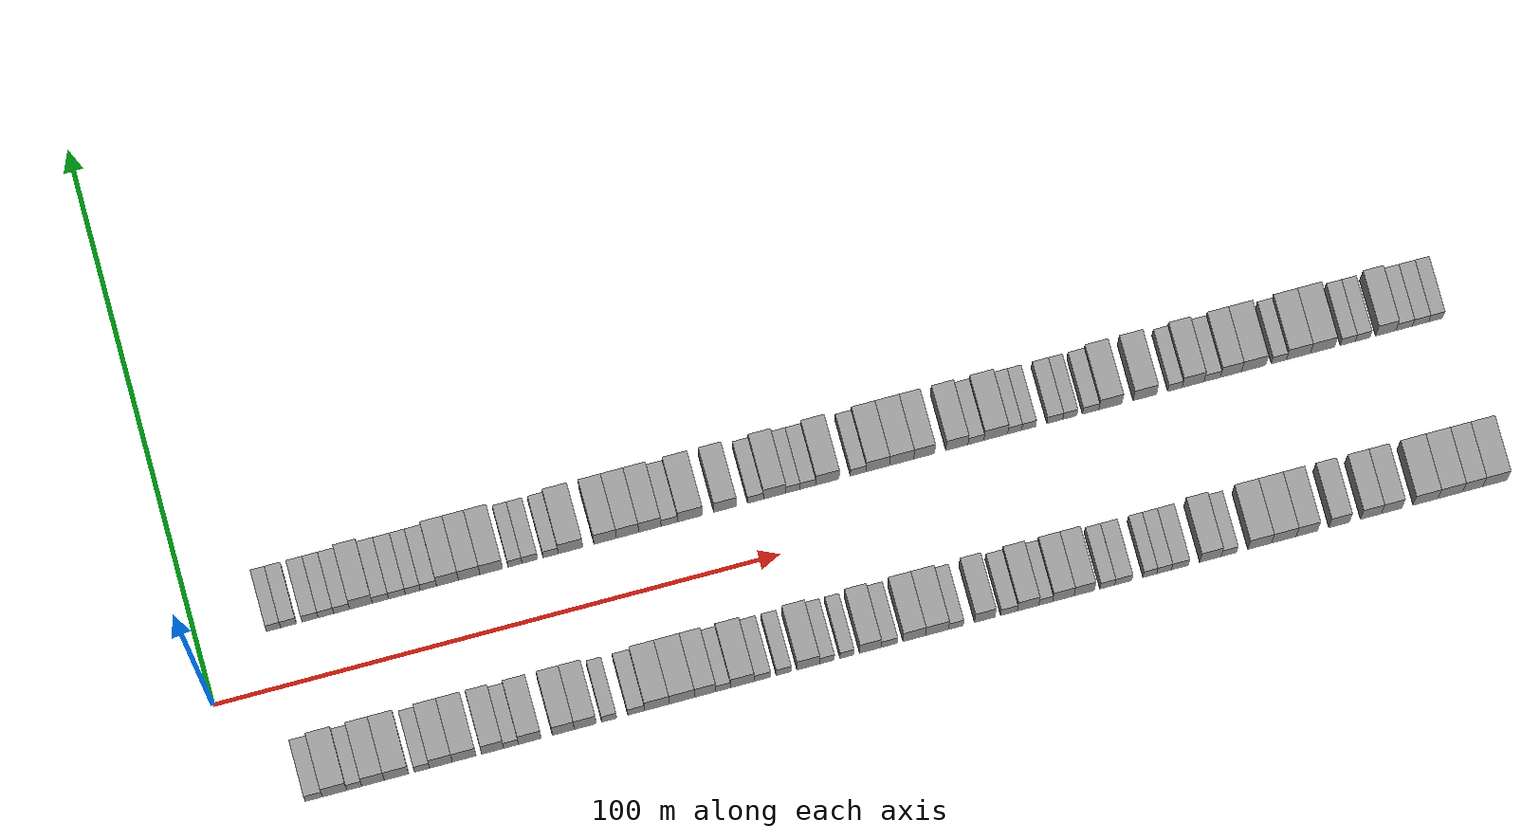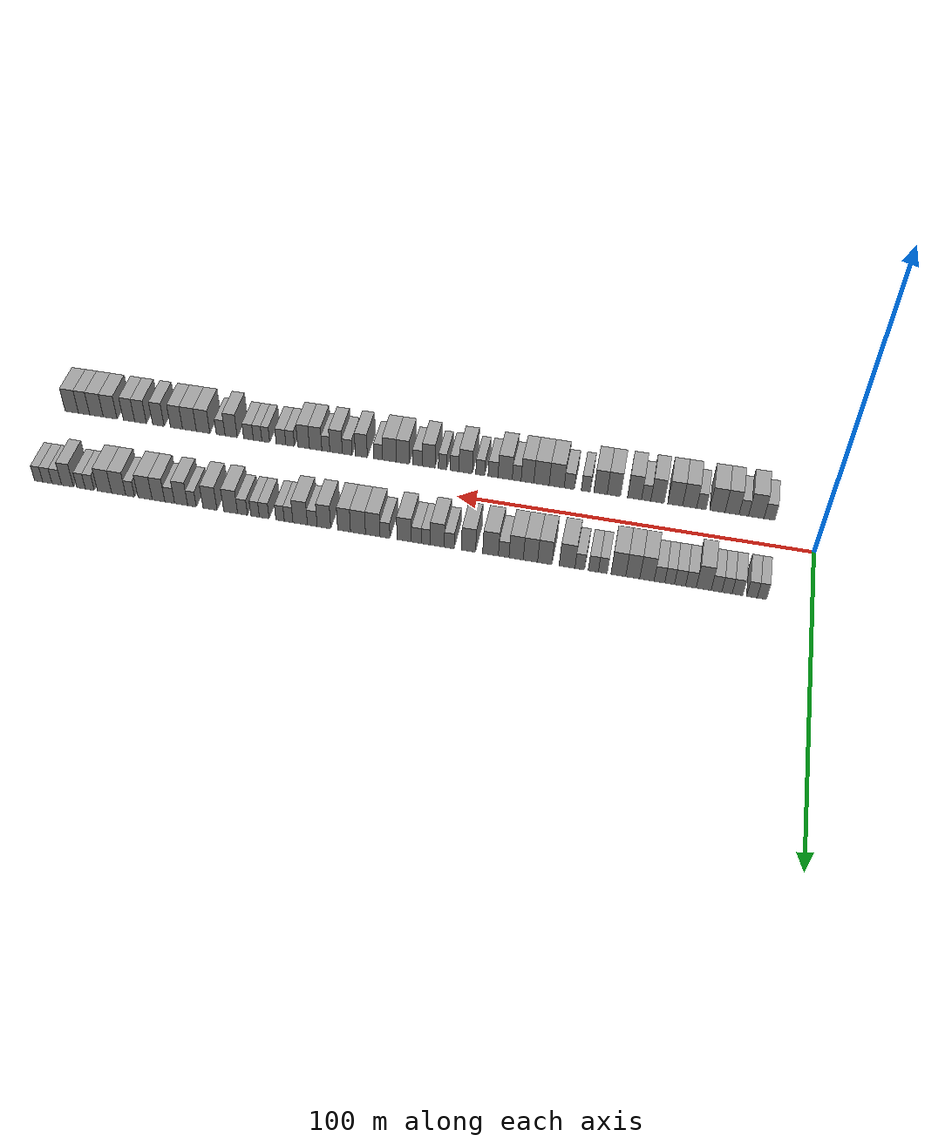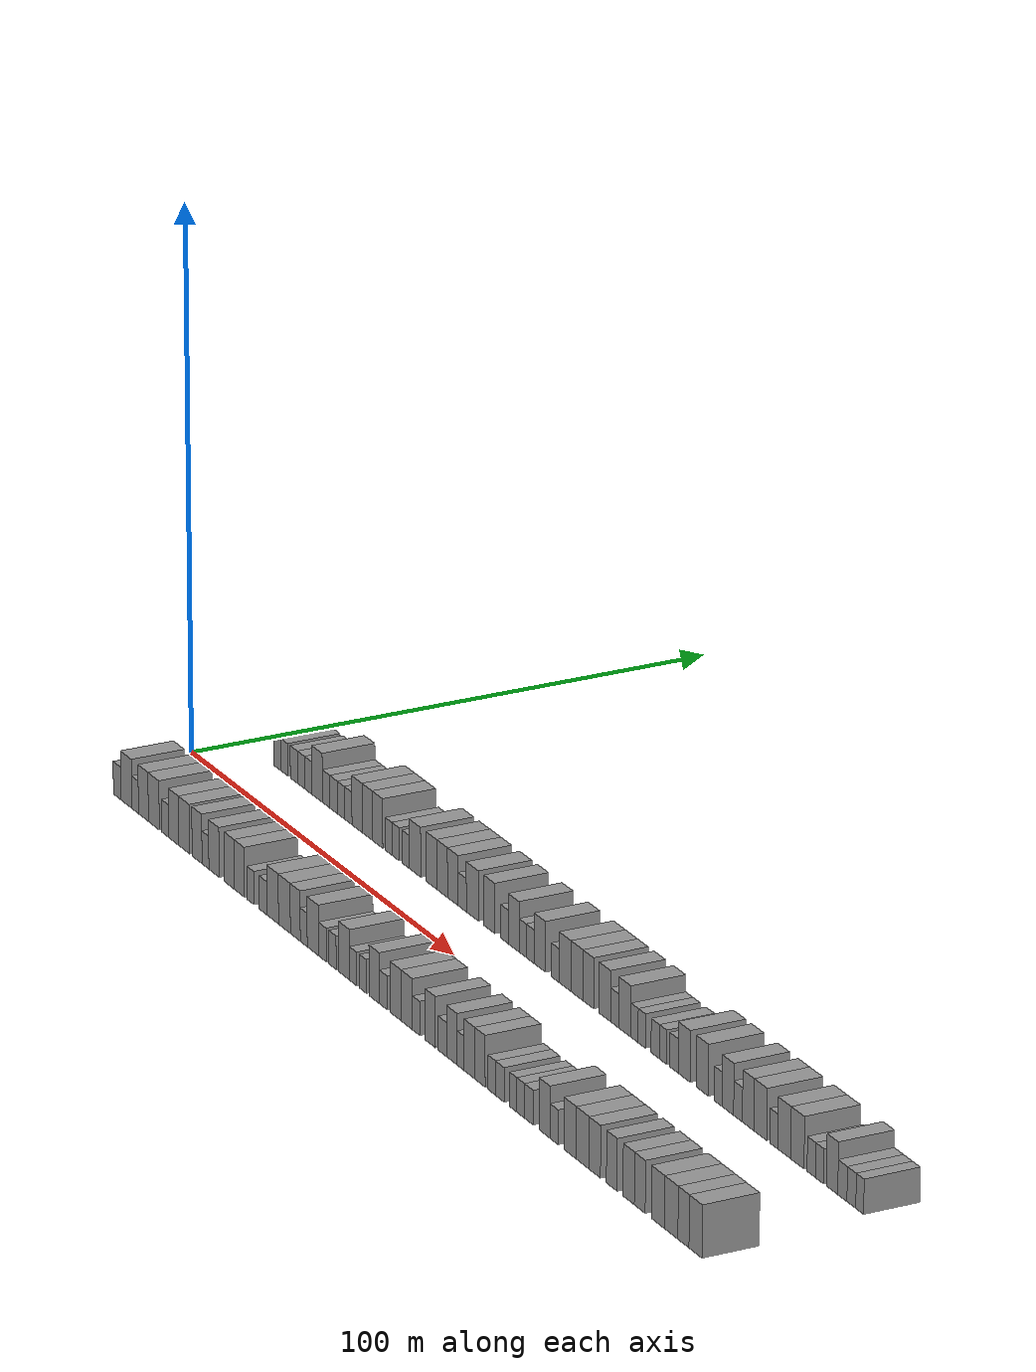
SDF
<sdf version="1.6">
 <world name="default">
  <scene>
   <sky><clouds><speed>12</speed></clouds></sky>
   <ambient>0.4 0.4 0.4 1</ambient>
   <background>0.7 0.7 0.7 1</background>
   <shadows>1</shadows>
  </scene>
  <gravity>0 0 -9.8066</gravity>
  <magnetic_field>6e-06 2.3e-05 -4.2e-05</magnetic_field>
  <physics default="0" name="default_physics" type="ode">
   <ode>
    <solver>
     <type>quick</type>
     <iters>10</iters>
     <sor>1.0</sor>
     <use_dynamic_moi_rescaling>0</use_dynamic_moi_rescaling>
    </solver>
    <constraints>
     <cfm>0</cfm>
     <erp>0.2</erp>
     <contact_max_correcting_vel>100</contact_max_correcting_vel>
     <contact_surface_layer>0.001</contact_surface_layer>
    </constraints>
   </ode>
   <max_step_size>0.004</max_step_size>
   <real_time_factor>1</real_time_factor>
   <real_time_update_rate>250</real_time_update_rate>
  </physics>
  <light name="sun" type="directional">
   <pose>0 0 10 0 0 0</pose>
   <diffuse>0.8 0.8 0.8 1</diffuse>
   <specular>0.2 0.2 0.2 1</specular>
   <attenuation>
    <range>1000</range>
    <constant>0.9</constant>
    <linear>0.01</linear>
    <quadratic>0.001</quadratic>
   </attenuation>
   <direction>-0.5 0.1 -0.9</direction>
  </light>
  <model name="building_1">
   <static>1</static>
   <pose>13.2395 15.0000 0 0.000000 0.000000 1.570796</pose>
   <link name="link">
    <pose>0 0 3.00 0 0 0</pose>
    <collision name="collision"><geometry><box><size>10.0000 2.4789 6.0000</size></box></geometry></collision>
    <visual name="visual">
     <cast_shadows>0</cast_shadows>
     <geometry><box><size>10.0000 2.4789 6.0000</size></box></geometry>
     <material>
      <script>
       <uri>model://grey_wall/materials/scripts</uri>
       <uri>model://grey_wall/materials/textures</uri>
       <name>vrc/grey_wall</name>
      </script>
     </material>
    </visual>
   </link>
  </model>
  <model name="building_2">
   <static>1</static>
   <pose>15.8671 15.0000 0 0.000000 0.000000 1.570796</pose>
   <link name="link">
    <pose>0 0 3.00 0 0 0</pose>
    <collision name="collision"><geometry><box><size>10.0000 2.7763 6.0000</size></box></geometry></collision>
    <visual name="visual">
     <cast_shadows>0</cast_shadows>
     <geometry><box><size>10.0000 2.7763 6.0000</size></box></geometry>
     <material>
      <script>
       <uri>model://grey_wall/materials/scripts</uri>
       <uri>model://grey_wall/materials/textures</uri>
       <name>vrc/grey_wall</name>
      </script>
     </material>
    </visual>
   </link>
  </model>
  <model name="building_3">
   <static>1</static>
   <pose>19.6746 15.0000 0 0.000000 0.000000 1.570796</pose>
   <link name="link">
    <pose>0 0 3.00 0 0 0</pose>
    <collision name="collision"><geometry><box><size>10.0000 2.8389 6.0000</size></box></geometry></collision>
    <visual name="visual">
     <cast_shadows>0</cast_shadows>
     <geometry><box><size>10.0000 2.8389 6.0000</size></box></geometry>
     <material>
      <script>
       <uri>model://grey_wall/materials/scripts</uri>
       <uri>model://grey_wall/materials/textures</uri>
       <name>vrc/grey_wall</name>
      </script>
     </material>
    </visual>
   </link>
  </model>
  <model name="building_4">
   <static>1</static>
   <pose>22.4632 15.0000 0 0.000000 0.000000 1.570796</pose>
   <link name="link">
    <pose>0 0 3.00 0 0 0</pose>
    <collision name="collision"><geometry><box><size>10.0000 2.7383 6.0000</size></box></geometry></collision>
    <visual name="visual">
     <cast_shadows>0</cast_shadows>
     <geometry><box><size>10.0000 2.7383 6.0000</size></box></geometry>
     <material>
      <script>
       <uri>model://grey_wall/materials/scripts</uri>
       <uri>model://grey_wall/materials/textures</uri>
       <name>vrc/grey_wall</name>
      </script>
     </material>
    </visual>
   </link>
  </model>
  <model name="building_5">
   <static>1</static>
   <pose>25.2391 15.0000 0 0.000000 0.000000 1.570796</pose>
   <link name="link">
    <pose>0 0 3.00 0 0 0</pose>
    <collision name="collision"><geometry><box><size>10.0000 2.8134 6.0000</size></box></geometry></collision>
    <visual name="visual">
     <cast_shadows>0</cast_shadows>
     <geometry><box><size>10.0000 2.8134 6.0000</size></box></geometry>
     <material>
      <script>
       <uri>model://grey_wall/materials/scripts</uri>
       <uri>model://grey_wall/materials/textures</uri>
       <name>vrc/grey_wall</name>
      </script>
     </material>
    </visual>
   </link>
  </model>
  <model name="building_6">
   <static>1</static>
   <pose>28.6374 15.0000 0 0.000000 0.000000 1.570796</pose>
   <link name="link">
    <pose>0 0 4.50 0 0 0</pose>
    <collision name="collision"><geometry><box><size>10.0000 3.9831 9.0000</size></box></geometry></collision>
    <visual name="visual">
     <cast_shadows>0</cast_shadows>
     <geometry><box><size>10.0000 3.9831 9.0000</size></box></geometry>
     <material>
      <script>
       <uri>model://grey_wall/materials/scripts</uri>
       <uri>model://grey_wall/materials/textures</uri>
       <name>vrc/grey_wall</name>
      </script>
     </material>
    </visual>
   </link>
  </model>
  <model name="building_7">
   <static>1</static>
   <pose>32.0669 15.0000 0 0.000000 0.000000 1.570796</pose>
   <link name="link">
    <pose>0 0 3.00 0 0 0</pose>
    <collision name="collision"><geometry><box><size>10.0000 2.8759 6.0000</size></box></geometry></collision>
    <visual name="visual">
     <cast_shadows>0</cast_shadows>
     <geometry><box><size>10.0000 2.8759 6.0000</size></box></geometry>
     <material>
      <script>
       <uri>model://grey_wall/materials/scripts</uri>
       <uri>model://grey_wall/materials/textures</uri>
       <name>vrc/grey_wall</name>
      </script>
     </material>
    </visual>
   </link>
  </model>
  <model name="building_8">
   <static>1</static>
   <pose>34.9849 15.0000 0 0.000000 0.000000 1.570796</pose>
   <link name="link">
    <pose>0 0 3.00 0 0 0</pose>
    <collision name="collision"><geometry><box><size>10.0000 2.9601 6.0000</size></box></geometry></collision>
    <visual name="visual">
     <cast_shadows>0</cast_shadows>
     <geometry><box><size>10.0000 2.9601 6.0000</size></box></geometry>
     <material>
      <script>
       <uri>model://grey_wall/materials/scripts</uri>
       <uri>model://grey_wall/materials/textures</uri>
       <name>vrc/grey_wall</name>
      </script>
     </material>
    </visual>
   </link>
  </model>
  <model name="building_9">
   <static>1</static>
   <pose>37.7684 15.0000 0 0.000000 0.000000 1.570796</pose>
   <link name="link">
    <pose>0 0 3.00 0 0 0</pose>
    <collision name="collision"><geometry><box><size>10.0000 2.6069 6.0000</size></box></geometry></collision>
    <visual name="visual">
     <cast_shadows>0</cast_shadows>
     <geometry><box><size>10.0000 2.6069 6.0000</size></box></geometry>
     <material>
      <script>
       <uri>model://grey_wall/materials/scripts</uri>
       <uri>model://grey_wall/materials/textures</uri>
       <name>vrc/grey_wall</name>
      </script>
     </material>
    </visual>
   </link>
  </model>
  <model name="building_10">
   <static>1</static>
   <pose>40.5030 15.0000 0 0.000000 0.000000 1.570796</pose>
   <link name="link">
    <pose>0 0 3.00 0 0 0</pose>
    <collision name="collision"><geometry><box><size>10.0000 2.8622 6.0000</size></box></geometry></collision>
    <visual name="visual">
     <cast_shadows>0</cast_shadows>
     <geometry><box><size>10.0000 2.8622 6.0000</size></box></geometry>
     <material>
      <script>
       <uri>model://grey_wall/materials/scripts</uri>
       <uri>model://grey_wall/materials/textures</uri>
       <name>vrc/grey_wall</name>
      </script>
     </material>
    </visual>
   </link>
  </model>
  <model name="building_11">
   <static>1</static>
   <pose>43.8686 15.0000 0 0.000000 0.000000 1.570796</pose>
   <link name="link">
    <pose>0 0 4.50 0 0 0</pose>
    <collision name="collision"><geometry><box><size>10.0000 3.8690 9.0000</size></box></geometry></collision>
    <visual name="visual">
     <cast_shadows>0</cast_shadows>
     <geometry><box><size>10.0000 3.8690 9.0000</size></box></geometry>
     <material>
      <script>
       <uri>model://grey_wall/materials/scripts</uri>
       <uri>model://grey_wall/materials/textures</uri>
       <name>vrc/grey_wall</name>
      </script>
     </material>
    </visual>
   </link>
  </model>
  <model name="building_12">
   <static>1</static>
   <pose>47.6986 15.0000 0 0.000000 0.000000 1.570796</pose>
   <link name="link">
    <pose>0 0 4.50 0 0 0</pose>
    <collision name="collision"><geometry><box><size>10.0000 3.7910 9.0000</size></box></geometry></collision>
    <visual name="visual">
     <cast_shadows>0</cast_shadows>
     <geometry><box><size>10.0000 3.7910 9.0000</size></box></geometry>
     <material>
      <script>
       <uri>model://grey_wall/materials/scripts</uri>
       <uri>model://grey_wall/materials/textures</uri>
       <name>vrc/grey_wall</name>
      </script>
     </material>
    </visual>
   </link>
  </model>
  <model name="building_13">
   <static>1</static>
   <pose>51.5891 15.0000 0 0.000000 0.000000 1.570796</pose>
   <link name="link">
    <pose>0 0 4.50 0 0 0</pose>
    <collision name="collision"><geometry><box><size>10.0000 3.9900 9.0000</size></box></geometry></collision>
    <visual name="visual">
     <cast_shadows>0</cast_shadows>
     <geometry><box><size>10.0000 3.9900 9.0000</size></box></geometry>
     <material>
      <script>
       <uri>model://grey_wall/materials/scripts</uri>
       <uri>model://grey_wall/materials/textures</uri>
       <name>vrc/grey_wall</name>
      </script>
     </material>
    </visual>
   </link>
  </model>
  <model name="building_14">
   <static>1</static>
   <pose>55.8028 15.0000 0 0.000000 0.000000 1.570796</pose>
   <link name="link">
    <pose>0 0 3.00 0 0 0</pose>
    <collision name="collision"><geometry><box><size>10.0000 2.4374 6.0000</size></box></geometry></collision>
    <visual name="visual">
     <cast_shadows>0</cast_shadows>
     <geometry><box><size>10.0000 2.4374 6.0000</size></box></geometry>
     <material>
      <script>
       <uri>model://grey_wall/materials/scripts</uri>
       <uri>model://grey_wall/materials/textures</uri>
       <name>vrc/grey_wall</name>
      </script>
     </material>
    </visual>
   </link>
  </model>
  <model name="building_15">
   <static>1</static>
   <pose>58.3949 15.0000 0 0.000000 0.000000 1.570796</pose>
   <link name="link">
    <pose>0 0 3.00 0 0 0</pose>
    <collision name="collision"><geometry><box><size>10.0000 2.7468 6.0000</size></box></geometry></collision>
    <visual name="visual">
     <cast_shadows>0</cast_shadows>
     <geometry><box><size>10.0000 2.7468 6.0000</size></box></geometry>
     <material>
      <script>
       <uri>model://grey_wall/materials/scripts</uri>
       <uri>model://grey_wall/materials/textures</uri>
       <name>vrc/grey_wall</name>
      </script>
     </material>
    </visual>
   </link>
  </model>
  <model name="building_16">
   <static>1</static>
   <pose>62.0917 15.0000 0 0.000000 0.000000 1.570796</pose>
   <link name="link">
    <pose>0 0 3.00 0 0 0</pose>
    <collision name="collision"><geometry><box><size>10.0000 2.6467 6.0000</size></box></geometry></collision>
    <visual name="visual">
     <cast_shadows>0</cast_shadows>
     <geometry><box><size>10.0000 2.6467 6.0000</size></box></geometry>
     <material>
      <script>
       <uri>model://grey_wall/materials/scripts</uri>
       <uri>model://grey_wall/materials/textures</uri>
       <name>vrc/grey_wall</name>
      </script>
     </material>
    </visual>
   </link>
  </model>
  <model name="building_17">
   <static>1</static>
   <pose>65.5790 15.0000 0 0.000000 0.000000 1.570796</pose>
   <link name="link">
    <pose>0 0 4.50 0 0 0</pose>
    <collision name="collision"><geometry><box><size>10.0000 4.3279 9.0000</size></box></geometry></collision>
    <visual name="visual">
     <cast_shadows>0</cast_shadows>
     <geometry><box><size>10.0000 4.3279 9.0000</size></box></geometry>
     <material>
      <script>
       <uri>model://grey_wall/materials/scripts</uri>
       <uri>model://grey_wall/materials/textures</uri>
       <name>vrc/grey_wall</name>
      </script>
     </material>
    </visual>
   </link>
  </model>
  <model name="building_18">
   <static>1</static>
   <pose>71.7157 15.0000 0 0.000000 0.000000 1.570796</pose>
   <link name="link">
    <pose>0 0 4.50 0 0 0</pose>
    <collision name="collision"><geometry><box><size>10.0000 3.9455 9.0000</size></box></geometry></collision>
    <visual name="visual">
     <cast_shadows>0</cast_shadows>
     <geometry><box><size>10.0000 3.9455 9.0000</size></box></geometry>
     <material>
      <script>
       <uri>model://grey_wall/materials/scripts</uri>
       <uri>model://grey_wall/materials/textures</uri>
       <name>vrc/grey_wall</name>
      </script>
     </material>
    </visual>
   </link>
  </model>
  <model name="building_19">
   <static>1</static>
   <pose>75.6649 15.0000 0 0.000000 0.000000 1.570796</pose>
   <link name="link">
    <pose>0 0 4.50 0 0 0</pose>
    <collision name="collision"><geometry><box><size>10.0000 3.9529 9.0000</size></box></geometry></collision>
    <visual name="visual">
     <cast_shadows>0</cast_shadows>
     <geometry><box><size>10.0000 3.9529 9.0000</size></box></geometry>
     <material>
      <script>
       <uri>model://grey_wall/materials/scripts</uri>
       <uri>model://grey_wall/materials/textures</uri>
       <name>vrc/grey_wall</name>
      </script>
     </material>
    </visual>
   </link>
  </model>
  <model name="building_20">
   <static>1</static>
   <pose>79.6231 15.0000 0 0.000000 0.000000 1.570796</pose>
   <link name="link">
    <pose>0 0 4.50 0 0 0</pose>
    <collision name="collision"><geometry><box><size>10.0000 3.9635 9.0000</size></box></geometry></collision>
    <visual name="visual">
     <cast_shadows>0</cast_shadows>
     <geometry><box><size>10.0000 3.9635 9.0000</size></box></geometry>
     <material>
      <script>
       <uri>model://grey_wall/materials/scripts</uri>
       <uri>model://grey_wall/materials/textures</uri>
       <name>vrc/grey_wall</name>
      </script>
     </material>
    </visual>
   </link>
  </model>
  <model name="building_21">
   <static>1</static>
   <pose>83.0800 15.0000 0 0.000000 0.000000 1.570796</pose>
   <link name="link">
    <pose>0 0 3.00 0 0 0</pose>
    <collision name="collision"><geometry><box><size>10.0000 2.9503 6.0000</size></box></geometry></collision>
    <visual name="visual">
     <cast_shadows>0</cast_shadows>
     <geometry><box><size>10.0000 2.9503 6.0000</size></box></geometry>
     <material>
      <script>
       <uri>model://grey_wall/materials/scripts</uri>
       <uri>model://grey_wall/materials/textures</uri>
       <name>vrc/grey_wall</name>
      </script>
     </material>
    </visual>
   </link>
  </model>
  <model name="building_22">
   <static>1</static>
   <pose>86.7415 15.0000 0 0.000000 0.000000 1.570796</pose>
   <link name="link">
    <pose>0 0 4.50 0 0 0</pose>
    <collision name="collision"><geometry><box><size>10.0000 4.3728 9.0000</size></box></geometry></collision>
    <visual name="visual">
     <cast_shadows>0</cast_shadows>
     <geometry><box><size>10.0000 4.3728 9.0000</size></box></geometry>
     <material>
      <script>
       <uri>model://grey_wall/materials/scripts</uri>
       <uri>model://grey_wall/materials/textures</uri>
       <name>vrc/grey_wall</name>
      </script>
     </material>
    </visual>
   </link>
  </model>
  <model name="building_23">
   <static>1</static>
   <pose>92.9218 15.0000 0 0.000000 0.000000 1.570796</pose>
   <link name="link">
    <pose>0 0 4.50 0 0 0</pose>
    <collision name="collision"><geometry><box><size>10.0000 3.9877 9.0000</size></box></geometry></collision>
    <visual name="visual">
     <cast_shadows>0</cast_shadows>
     <geometry><box><size>10.0000 3.9877 9.0000</size></box></geometry>
     <material>
      <script>
       <uri>model://grey_wall/materials/scripts</uri>
       <uri>model://grey_wall/materials/textures</uri>
       <name>vrc/grey_wall</name>
      </script>
     </material>
    </visual>
   </link>
  </model>
  <model name="building_24">
   <static>1</static>
   <pose>98.3099 15.0000 0 0.000000 0.000000 1.570796</pose>
   <link name="link">
    <pose>0 0 3.00 0 0 0</pose>
    <collision name="collision"><geometry><box><size>10.0000 2.7886 6.0000</size></box></geometry></collision>
    <visual name="visual">
     <cast_shadows>0</cast_shadows>
     <geometry><box><size>10.0000 2.7886 6.0000</size></box></geometry>
     <material>
      <script>
       <uri>model://grey_wall/materials/scripts</uri>
       <uri>model://grey_wall/materials/textures</uri>
       <name>vrc/grey_wall</name>
      </script>
     </material>
    </visual>
   </link>
  </model>
  <model name="building_25">
   <static>1</static>
   <pose>101.6872 15.0000 0 0.000000 0.000000 1.570796</pose>
   <link name="link">
    <pose>0 0 4.50 0 0 0</pose>
    <collision name="collision"><geometry><box><size>10.0000 3.9659 9.0000</size></box></geometry></collision>
    <visual name="visual">
     <cast_shadows>0</cast_shadows>
     <geometry><box><size>10.0000 3.9659 9.0000</size></box></geometry>
     <material>
      <script>
       <uri>model://grey_wall/materials/scripts</uri>
       <uri>model://grey_wall/materials/textures</uri>
       <name>vrc/grey_wall</name>
      </script>
     </material>
    </visual>
   </link>
  </model>
  <model name="building_26">
   <static>1</static>
   <pose>104.9479 15.0000 0 0.000000 0.000000 1.570796</pose>
   <link name="link">
    <pose>0 0 3.00 0 0 0</pose>
    <collision name="collision"><geometry><box><size>10.0000 2.5557 6.0000</size></box></geometry></collision>
    <visual name="visual">
     <cast_shadows>0</cast_shadows>
     <geometry><box><size>10.0000 2.5557 6.0000</size></box></geometry>
     <material>
      <script>
       <uri>model://grey_wall/materials/scripts</uri>
       <uri>model://grey_wall/materials/textures</uri>
       <name>vrc/grey_wall</name>
      </script>
     </material>
    </visual>
   </link>
  </model>
  <model name="building_27">
   <static>1</static>
   <pose>107.5997 15.0000 0 0.000000 0.000000 1.570796</pose>
   <link name="link">
    <pose>0 0 3.00 0 0 0</pose>
    <collision name="collision"><geometry><box><size>10.0000 2.7478 6.0000</size></box></geometry></collision>
    <visual name="visual">
     <cast_shadows>0</cast_shadows>
     <geometry><box><size>10.0000 2.7478 6.0000</size></box></geometry>
     <material>
      <script>
       <uri>model://grey_wall/materials/scripts</uri>
       <uri>model://grey_wall/materials/textures</uri>
       <name>vrc/grey_wall</name>
      </script>
     </material>
    </visual>
   </link>
  </model>
  <model name="building_28">
   <static>1</static>
   <pose>111.0488 15.0000 0 0.000000 0.000000 1.570796</pose>
   <link name="link">
    <pose>0 0 4.50 0 0 0</pose>
    <collision name="collision"><geometry><box><size>10.0000 4.1505 9.0000</size></box></geometry></collision>
    <visual name="visual">
     <cast_shadows>0</cast_shadows>
     <geometry><box><size>10.0000 4.1505 9.0000</size></box></geometry>
     <material>
      <script>
       <uri>model://grey_wall/materials/scripts</uri>
       <uri>model://grey_wall/materials/textures</uri>
       <name>vrc/grey_wall</name>
      </script>
     </material>
    </visual>
   </link>
  </model>
  <model name="building_29">
   <static>1</static>
   <pose>116.5231 15.0000 0 0.000000 0.000000 1.570796</pose>
   <link name="link">
    <pose>0 0 3.00 0 0 0</pose>
    <collision name="collision"><geometry><box><size>10.0000 2.7981 6.0000</size></box></geometry></collision>
    <visual name="visual">
     <cast_shadows>0</cast_shadows>
     <geometry><box><size>10.0000 2.7981 6.0000</size></box></geometry>
     <material>
      <script>
       <uri>model://grey_wall/materials/scripts</uri>
       <uri>model://grey_wall/materials/textures</uri>
       <name>vrc/grey_wall</name>
      </script>
     </material>
    </visual>
   </link>
  </model>
  <model name="building_30">
   <static>1</static>
   <pose>120.0027 15.0000 0 0.000000 0.000000 1.570796</pose>
   <link name="link">
    <pose>0 0 4.50 0 0 0</pose>
    <collision name="collision"><geometry><box><size>10.0000 4.1611 9.0000</size></box></geometry></collision>
    <visual name="visual">
     <cast_shadows>0</cast_shadows>
     <geometry><box><size>10.0000 4.1611 9.0000</size></box></geometry>
     <material>
      <script>
       <uri>model://grey_wall/materials/scripts</uri>
       <uri>model://grey_wall/materials/textures</uri>
       <name>vrc/grey_wall</name>
      </script>
     </material>
    </visual>
   </link>
  </model>
  <model name="building_31">
   <static>1</static>
   <pose>124.2219 15.0000 0 0.000000 0.000000 1.570796</pose>
   <link name="link">
    <pose>0 0 4.50 0 0 0</pose>
    <collision name="collision"><geometry><box><size>10.0000 4.2773 9.0000</size></box></geometry></collision>
    <visual name="visual">
     <cast_shadows>0</cast_shadows>
     <geometry><box><size>10.0000 4.2773 9.0000</size></box></geometry>
     <material>
      <script>
       <uri>model://grey_wall/materials/scripts</uri>
       <uri>model://grey_wall/materials/textures</uri>
       <name>vrc/grey_wall</name>
      </script>
     </material>
    </visual>
   </link>
  </model>
  <model name="building_32">
   <static>1</static>
   <pose>128.2122 15.0000 0 0.000000 0.000000 1.570796</pose>
   <link name="link">
    <pose>0 0 4.50 0 0 0</pose>
    <collision name="collision"><geometry><box><size>10.0000 3.7033 9.0000</size></box></geometry></collision>
    <visual name="visual">
     <cast_shadows>0</cast_shadows>
     <geometry><box><size>10.0000 3.7033 9.0000</size></box></geometry>
     <material>
      <script>
       <uri>model://grey_wall/materials/scripts</uri>
       <uri>model://grey_wall/materials/textures</uri>
       <name>vrc/grey_wall</name>
      </script>
     </material>
    </visual>
   </link>
  </model>
  <model name="building_33">
   <static>1</static>
   <pose>134.0281 15.0000 0 0.000000 0.000000 1.570796</pose>
   <link name="link">
    <pose>0 0 4.50 0 0 0</pose>
    <collision name="collision"><geometry><box><size>10.0000 3.9285 9.0000</size></box></geometry></collision>
    <visual name="visual">
     <cast_shadows>0</cast_shadows>
     <geometry><box><size>10.0000 3.9285 9.0000</size></box></geometry>
     <material>
      <script>
       <uri>model://grey_wall/materials/scripts</uri>
       <uri>model://grey_wall/materials/textures</uri>
       <name>vrc/grey_wall</name>
      </script>
     </material>
    </visual>
   </link>
  </model>
  <model name="building_34">
   <static>1</static>
   <pose>137.4024 15.0000 0 0.000000 0.000000 1.570796</pose>
   <link name="link">
    <pose>0 0 3.00 0 0 0</pose>
    <collision name="collision"><geometry><box><size>10.0000 2.8201 6.0000</size></box></geometry></collision>
    <visual name="visual">
     <cast_shadows>0</cast_shadows>
     <geometry><box><size>10.0000 2.8201 6.0000</size></box></geometry>
     <material>
      <script>
       <uri>model://grey_wall/materials/scripts</uri>
       <uri>model://grey_wall/materials/textures</uri>
       <name>vrc/grey_wall</name>
      </script>
     </material>
    </visual>
   </link>
  </model>
  <model name="building_35">
   <static>1</static>
   <pose>140.9218 15.0000 0 0.000000 0.000000 1.570796</pose>
   <link name="link">
    <pose>0 0 4.50 0 0 0</pose>
    <collision name="collision"><geometry><box><size>10.0000 4.2188 9.0000</size></box></geometry></collision>
    <visual name="visual">
     <cast_shadows>0</cast_shadows>
     <geometry><box><size>10.0000 4.2188 9.0000</size></box></geometry>
     <material>
      <script>
       <uri>model://grey_wall/materials/scripts</uri>
       <uri>model://grey_wall/materials/textures</uri>
       <name>vrc/grey_wall</name>
      </script>
     </material>
    </visual>
   </link>
  </model>
  <model name="building_36">
   <static>1</static>
   <pose>144.2823 15.0000 0 0.000000 0.000000 1.570796</pose>
   <link name="link">
    <pose>0 0 3.00 0 0 0</pose>
    <collision name="collision"><geometry><box><size>10.0000 2.5022 6.0000</size></box></geometry></collision>
    <visual name="visual">
     <cast_shadows>0</cast_shadows>
     <geometry><box><size>10.0000 2.5022 6.0000</size></box></geometry>
     <material>
      <script>
       <uri>model://grey_wall/materials/scripts</uri>
       <uri>model://grey_wall/materials/textures</uri>
       <name>vrc/grey_wall</name>
      </script>
     </material>
    </visual>
   </link>
  </model>
  <model name="building_37">
   <static>1</static>
   <pose>146.7636 15.0000 0 0.000000 0.000000 1.570796</pose>
   <link name="link">
    <pose>0 0 3.00 0 0 0</pose>
    <collision name="collision"><geometry><box><size>10.0000 2.4604 6.0000</size></box></geometry></collision>
    <visual name="visual">
     <cast_shadows>0</cast_shadows>
     <geometry><box><size>10.0000 2.4604 6.0000</size></box></geometry>
     <material>
      <script>
       <uri>model://grey_wall/materials/scripts</uri>
       <uri>model://grey_wall/materials/textures</uri>
       <name>vrc/grey_wall</name>
      </script>
     </material>
    </visual>
   </link>
  </model>
  <model name="building_38">
   <static>1</static>
   <pose>151.4189 15.0000 0 0.000000 0.000000 1.570796</pose>
   <link name="link">
    <pose>0 0 3.00 0 0 0</pose>
    <collision name="collision"><geometry><box><size>10.0000 2.8504 6.0000</size></box></geometry></collision>
    <visual name="visual">
     <cast_shadows>0</cast_shadows>
     <geometry><box><size>10.0000 2.8504 6.0000</size></box></geometry>
     <material>
      <script>
       <uri>model://grey_wall/materials/scripts</uri>
       <uri>model://grey_wall/materials/textures</uri>
       <name>vrc/grey_wall</name>
      </script>
     </material>
    </visual>
   </link>
  </model>
  <model name="building_39">
   <static>1</static>
   <pose>154.0806 15.0000 0 0.000000 0.000000 1.570796</pose>
   <link name="link">
    <pose>0 0 3.00 0 0 0</pose>
    <collision name="collision"><geometry><box><size>10.0000 2.4729 6.0000</size></box></geometry></collision>
    <visual name="visual">
     <cast_shadows>0</cast_shadows>
     <geometry><box><size>10.0000 2.4729 6.0000</size></box></geometry>
     <material>
      <script>
       <uri>model://grey_wall/materials/scripts</uri>
       <uri>model://grey_wall/materials/textures</uri>
       <name>vrc/grey_wall</name>
      </script>
     </material>
    </visual>
   </link>
  </model>
  <model name="building_40">
   <static>1</static>
   <pose>157.7672 15.0000 0 0.000000 0.000000 1.570796</pose>
   <link name="link">
    <pose>0 0 3.00 0 0 0</pose>
    <collision name="collision"><geometry><box><size>10.0000 2.9003 6.0000</size></box></geometry></collision>
    <visual name="visual">
     <cast_shadows>0</cast_shadows>
     <geometry><box><size>10.0000 2.9003 6.0000</size></box></geometry>
     <material>
      <script>
       <uri>model://grey_wall/materials/scripts</uri>
       <uri>model://grey_wall/materials/textures</uri>
       <name>vrc/grey_wall</name>
      </script>
     </material>
    </visual>
   </link>
  </model>
  <model name="building_41">
   <static>1</static>
   <pose>161.2655 15.0000 0 0.000000 0.000000 1.570796</pose>
   <link name="link">
    <pose>0 0 4.50 0 0 0</pose>
    <collision name="collision"><geometry><box><size>10.0000 4.0963 9.0000</size></box></geometry></collision>
    <visual name="visual">
     <cast_shadows>0</cast_shadows>
     <geometry><box><size>10.0000 4.0963 9.0000</size></box></geometry>
     <material>
      <script>
       <uri>model://grey_wall/materials/scripts</uri>
       <uri>model://grey_wall/materials/textures</uri>
       <name>vrc/grey_wall</name>
      </script>
     </material>
    </visual>
   </link>
  </model>
  <model name="building_42">
   <static>1</static>
   <pose>167.3902 15.0000 0 0.000000 0.000000 1.570796</pose>
   <link name="link">
    <pose>0 0 4.50 0 0 0</pose>
    <collision name="collision"><geometry><box><size>10.0000 4.1531 9.0000</size></box></geometry></collision>
    <visual name="visual">
     <cast_shadows>0</cast_shadows>
     <geometry><box><size>10.0000 4.1531 9.0000</size></box></geometry>
     <material>
      <script>
       <uri>model://grey_wall/materials/scripts</uri>
       <uri>model://grey_wall/materials/textures</uri>
       <name>vrc/grey_wall</name>
      </script>
     </material>
    </visual>
   </link>
  </model>
  <model name="building_43">
   <static>1</static>
   <pose>172.7508 15.0000 0 0.000000 0.000000 1.570796</pose>
   <link name="link">
    <pose>0 0 3.00 0 0 0</pose>
    <collision name="collision"><geometry><box><size>10.0000 2.5681 6.0000</size></box></geometry></collision>
    <visual name="visual">
     <cast_shadows>0</cast_shadows>
     <geometry><box><size>10.0000 2.5681 6.0000</size></box></geometry>
     <material>
      <script>
       <uri>model://grey_wall/materials/scripts</uri>
       <uri>model://grey_wall/materials/textures</uri>
       <name>vrc/grey_wall</name>
      </script>
     </material>
    </visual>
   </link>
  </model>
  <model name="building_44">
   <static>1</static>
   <pose>175.9808 15.0000 0 0.000000 0.000000 1.570796</pose>
   <link name="link">
    <pose>0 0 4.50 0 0 0</pose>
    <collision name="collision"><geometry><box><size>10.0000 3.8918 9.0000</size></box></geometry></collision>
    <visual name="visual">
     <cast_shadows>0</cast_shadows>
     <geometry><box><size>10.0000 3.8918 9.0000</size></box></geometry>
     <material>
      <script>
       <uri>model://grey_wall/materials/scripts</uri>
       <uri>model://grey_wall/materials/textures</uri>
       <name>vrc/grey_wall</name>
      </script>
     </material>
    </visual>
   </link>
  </model>
  <model name="building_45">
   <static>1</static>
   <pose>179.3925 15.0000 0 0.000000 0.000000 1.570796</pose>
   <link name="link">
    <pose>0 0 3.00 0 0 0</pose>
    <collision name="collision"><geometry><box><size>10.0000 2.9315 6.0000</size></box></geometry></collision>
    <visual name="visual">
     <cast_shadows>0</cast_shadows>
     <geometry><box><size>10.0000 2.9315 6.0000</size></box></geometry>
     <material>
      <script>
       <uri>model://grey_wall/materials/scripts</uri>
       <uri>model://grey_wall/materials/textures</uri>
       <name>vrc/grey_wall</name>
      </script>
     </material>
    </visual>
   </link>
  </model>
  <model name="building_46">
   <static>1</static>
   <pose>182.7444 15.0000 0 0.000000 0.000000 1.570796</pose>
   <link name="link">
    <pose>0 0 4.50 0 0 0</pose>
    <collision name="collision"><geometry><box><size>10.0000 3.7723 9.0000</size></box></geometry></collision>
    <visual name="visual">
     <cast_shadows>0</cast_shadows>
     <geometry><box><size>10.0000 3.7723 9.0000</size></box></geometry>
     <material>
      <script>
       <uri>model://grey_wall/materials/scripts</uri>
       <uri>model://grey_wall/materials/textures</uri>
       <name>vrc/grey_wall</name>
      </script>
     </material>
    </visual>
   </link>
  </model>
  <model name="building_47">
   <static>1</static>
   <pose>186.7781 15.0000 0 0.000000 0.000000 1.570796</pose>
   <link name="link">
    <pose>0 0 4.50 0 0 0</pose>
    <collision name="collision"><geometry><box><size>10.0000 4.2951 9.0000</size></box></geometry></collision>
    <visual name="visual">
     <cast_shadows>0</cast_shadows>
     <geometry><box><size>10.0000 4.2951 9.0000</size></box></geometry>
     <material>
      <script>
       <uri>model://grey_wall/materials/scripts</uri>
       <uri>model://grey_wall/materials/textures</uri>
       <name>vrc/grey_wall</name>
      </script>
     </material>
    </visual>
   </link>
  </model>
  <model name="building_48">
   <static>1</static>
   <pose>191.2633 15.0000 0 0.000000 0.000000 1.570796</pose>
   <link name="link">
    <pose>0 0 3.00 0 0 0</pose>
    <collision name="collision"><geometry><box><size>10.0000 2.6752 6.0000</size></box></geometry></collision>
    <visual name="visual">
     <cast_shadows>0</cast_shadows>
     <geometry><box><size>10.0000 2.6752 6.0000</size></box></geometry>
     <material>
      <script>
       <uri>model://grey_wall/materials/scripts</uri>
       <uri>model://grey_wall/materials/textures</uri>
       <name>vrc/grey_wall</name>
      </script>
     </material>
    </visual>
   </link>
  </model>
  <model name="building_49">
   <static>1</static>
   <pose>194.7339 15.0000 0 0.000000 0.000000 1.570796</pose>
   <link name="link">
    <pose>0 0 4.50 0 0 0</pose>
    <collision name="collision"><geometry><box><size>10.0000 4.2661 9.0000</size></box></geometry></collision>
    <visual name="visual">
     <cast_shadows>0</cast_shadows>
     <geometry><box><size>10.0000 4.2661 9.0000</size></box></geometry>
     <material>
      <script>
       <uri>model://grey_wall/materials/scripts</uri>
       <uri>model://grey_wall/materials/textures</uri>
       <name>vrc/grey_wall</name>
      </script>
     </material>
    </visual>
   </link>
  </model>
  <model name="building_50">
   <static>1</static>
   <pose>199.0243 15.0000 0 0.000000 0.000000 1.570796</pose>
   <link name="link">
    <pose>0 0 4.50 0 0 0</pose>
    <collision name="collision"><geometry><box><size>10.0000 4.3147 9.0000</size></box></geometry></collision>
    <visual name="visual">
     <cast_shadows>0</cast_shadows>
     <geometry><box><size>10.0000 4.3147 9.0000</size></box></geometry>
     <material>
      <script>
       <uri>model://grey_wall/materials/scripts</uri>
       <uri>model://grey_wall/materials/textures</uri>
       <name>vrc/grey_wall</name>
      </script>
     </material>
    </visual>
   </link>
  </model>
  <model name="building_51">
   <static>1</static>
   <pose>203.5385 15.0000 0 0.000000 0.000000 1.570796</pose>
   <link name="link">
    <pose>0 0 3.00 0 0 0</pose>
    <collision name="collision"><geometry><box><size>10.0000 2.7138 6.0000</size></box></geometry></collision>
    <visual name="visual">
     <cast_shadows>0</cast_shadows>
     <geometry><box><size>10.0000 2.7138 6.0000</size></box></geometry>
     <material>
      <script>
       <uri>model://grey_wall/materials/scripts</uri>
       <uri>model://grey_wall/materials/textures</uri>
       <name>vrc/grey_wall</name>
      </script>
     </material>
    </visual>
   </link>
  </model>
  <model name="building_52">
   <static>1</static>
   <pose>206.1987 15.0000 0 0.000000 0.000000 1.570796</pose>
   <link name="link">
    <pose>0 0 3.00 0 0 0</pose>
    <collision name="collision"><geometry><box><size>10.0000 2.6066 6.0000</size></box></geometry></collision>
    <visual name="visual">
     <cast_shadows>0</cast_shadows>
     <geometry><box><size>10.0000 2.6066 6.0000</size></box></geometry>
     <material>
      <script>
       <uri>model://grey_wall/materials/scripts</uri>
       <uri>model://grey_wall/materials/textures</uri>
       <name>vrc/grey_wall</name>
      </script>
     </material>
    </visual>
   </link>
  </model>
  <model name="building_53">
   <static>1</static>
   <pose>210.3247 15.0000 0 0.000000 0.000000 1.570796</pose>
   <link name="link">
    <pose>0 0 4.50 0 0 0</pose>
    <collision name="collision"><geometry><box><size>10.0000 3.6454 9.0000</size></box></geometry></collision>
    <visual name="visual">
     <cast_shadows>0</cast_shadows>
     <geometry><box><size>10.0000 3.6454 9.0000</size></box></geometry>
     <material>
      <script>
       <uri>model://grey_wall/materials/scripts</uri>
       <uri>model://grey_wall/materials/textures</uri>
       <name>vrc/grey_wall</name>
      </script>
     </material>
    </visual>
   </link>
  </model>
  <model name="building_54">
   <static>1</static>
   <pose>213.6157 15.0000 0 0.000000 0.000000 1.570796</pose>
   <link name="link">
    <pose>0 0 3.00 0 0 0</pose>
    <collision name="collision"><geometry><box><size>10.0000 2.9364 6.0000</size></box></geometry></collision>
    <visual name="visual">
     <cast_shadows>0</cast_shadows>
     <geometry><box><size>10.0000 2.9364 6.0000</size></box></geometry>
     <material>
      <script>
       <uri>model://grey_wall/materials/scripts</uri>
       <uri>model://grey_wall/materials/textures</uri>
       <name>vrc/grey_wall</name>
      </script>
     </material>
    </visual>
   </link>
  </model>
  <model name="building_55">
   <static>1</static>
   <pose>216.5117 15.0000 0 0.000000 0.000000 1.570796</pose>
   <link name="link">
    <pose>0 0 3.00 0 0 0</pose>
    <collision name="collision"><geometry><box><size>10.0000 2.8557 6.0000</size></box></geometry></collision>
    <visual name="visual">
     <cast_shadows>0</cast_shadows>
     <geometry><box><size>10.0000 2.8557 6.0000</size></box></geometry>
     <material>
      <script>
       <uri>model://grey_wall/materials/scripts</uri>
       <uri>model://grey_wall/materials/textures</uri>
       <name>vrc/grey_wall</name>
      </script>
     </material>
    </visual>
   </link>
  </model>
  <model name="building_56">
   <static>1</static>
   <pose>219.1995 15.0000 0 0.000000 0.000000 1.570796</pose>
   <link name="link">
    <pose>0 0 3.00 0 0 0</pose>
    <collision name="collision"><geometry><box><size>10.0000 2.5199 6.0000</size></box></geometry></collision>
    <visual name="visual">
     <cast_shadows>0</cast_shadows>
     <geometry><box><size>10.0000 2.5199 6.0000</size></box></geometry>
     <material>
      <script>
       <uri>model://grey_wall/materials/scripts</uri>
       <uri>model://grey_wall/materials/textures</uri>
       <name>vrc/grey_wall</name>
      </script>
     </material>
    </visual>
   </link>
  </model>
  <model name="building_57">
   <static>1</static>
   <pose>12.4929 -15.0000 0 0.000000 0.000000 1.570796</pose>
   <link name="link">
    <pose>0 0 3.00 0 0 0</pose>
    <collision name="collision"><geometry><box><size>10.0000 2.9857 6.0000</size></box></geometry></collision>
    <visual name="visual">
     <cast_shadows>0</cast_shadows>
     <geometry><box><size>10.0000 2.9857 6.0000</size></box></geometry>
     <material>
      <script>
       <uri>model://grey_wall/materials/scripts</uri>
       <uri>model://grey_wall/materials/textures</uri>
       <name>vrc/grey_wall</name>
      </script>
     </material>
    </visual>
   </link>
  </model>
  <model name="building_58">
   <static>1</static>
   <pose>16.1496 -15.0000 0 0.000000 0.000000 1.570796</pose>
   <link name="link">
    <pose>0 0 4.50 0 0 0</pose>
    <collision name="collision"><geometry><box><size>10.0000 4.3278 9.0000</size></box></geometry></collision>
    <visual name="visual">
     <cast_shadows>0</cast_shadows>
     <geometry><box><size>10.0000 4.3278 9.0000</size></box></geometry>
     <material>
      <script>
       <uri>model://grey_wall/materials/scripts</uri>
       <uri>model://grey_wall/materials/textures</uri>
       <name>vrc/grey_wall</name>
      </script>
     </material>
    </visual>
   </link>
  </model>
  <model name="building_59">
   <static>1</static>
   <pose>19.6313 -15.0000 0 0.000000 0.000000 1.570796</pose>
   <link name="link">
    <pose>0 0 3.00 0 0 0</pose>
    <collision name="collision"><geometry><box><size>10.0000 2.6355 6.0000</size></box></geometry></collision>
    <visual name="visual">
     <cast_shadows>0</cast_shadows>
     <geometry><box><size>10.0000 2.6355 6.0000</size></box></geometry>
     <material>
      <script>
       <uri>model://grey_wall/materials/scripts</uri>
       <uri>model://grey_wall/materials/textures</uri>
       <name>vrc/grey_wall</name>
      </script>
     </material>
    </visual>
   </link>
  </model>
  <model name="building_60">
   <static>1</static>
   <pose>22.9120 -15.0000 0 0.000000 0.000000 1.570796</pose>
   <link name="link">
    <pose>0 0 4.50 0 0 0</pose>
    <collision name="collision"><geometry><box><size>10.0000 3.9260 9.0000</size></box></geometry></collision>
    <visual name="visual">
     <cast_shadows>0</cast_shadows>
     <geometry><box><size>10.0000 3.9260 9.0000</size></box></geometry>
     <material>
      <script>
       <uri>model://grey_wall/materials/scripts</uri>
       <uri>model://grey_wall/materials/textures</uri>
       <name>vrc/grey_wall</name>
      </script>
     </material>
    </visual>
   </link>
  </model>
  <model name="building_61">
   <static>1</static>
   <pose>27.0262 -15.0000 0 0.000000 0.000000 1.570796</pose>
   <link name="link">
    <pose>0 0 4.50 0 0 0</pose>
    <collision name="collision"><geometry><box><size>10.0000 4.3025 9.0000</size></box></geometry></collision>
    <visual name="visual">
     <cast_shadows>0</cast_shadows>
     <geometry><box><size>10.0000 4.3025 9.0000</size></box></geometry>
     <material>
      <script>
       <uri>model://grey_wall/materials/scripts</uri>
       <uri>model://grey_wall/materials/textures</uri>
       <name>vrc/grey_wall</name>
      </script>
     </material>
    </visual>
   </link>
  </model>
  <model name="building_62">
   <static>1</static>
   <pose>31.5069 -15.0000 0 0.000000 0.000000 1.570796</pose>
   <link name="link">
    <pose>0 0 3.00 0 0 0</pose>
    <collision name="collision"><geometry><box><size>10.0000 2.6589 6.0000</size></box></geometry></collision>
    <visual name="visual">
     <cast_shadows>0</cast_shadows>
     <geometry><box><size>10.0000 2.6589 6.0000</size></box></geometry>
     <material>
      <script>
       <uri>model://grey_wall/materials/scripts</uri>
       <uri>model://grey_wall/materials/textures</uri>
       <name>vrc/grey_wall</name>
      </script>
     </material>
    </visual>
   </link>
  </model>
  <model name="building_63">
   <static>1</static>
   <pose>34.8278 -15.0000 0 0.000000 0.000000 1.570796</pose>
   <link name="link">
    <pose>0 0 4.50 0 0 0</pose>
    <collision name="collision"><geometry><box><size>10.0000 3.9829 9.0000</size></box></geometry></collision>
    <visual name="visual">
     <cast_shadows>0</cast_shadows>
     <geometry><box><size>10.0000 3.9829 9.0000</size></box></geometry>
     <material>
      <script>
       <uri>model://grey_wall/materials/scripts</uri>
       <uri>model://grey_wall/materials/textures</uri>
       <name>vrc/grey_wall</name>
      </script>
     </material>
    </visual>
   </link>
  </model>
  <model name="building_64">
   <static>1</static>
   <pose>38.9074 -15.0000 0 0.000000 0.000000 1.570796</pose>
   <link name="link">
    <pose>0 0 4.50 0 0 0</pose>
    <collision name="collision"><geometry><box><size>10.0000 4.1764 9.0000</size></box></geometry></collision>
    <visual name="visual">
     <cast_shadows>0</cast_shadows>
     <geometry><box><size>10.0000 4.1764 9.0000</size></box></geometry>
     <material>
      <script>
       <uri>model://grey_wall/materials/scripts</uri>
       <uri>model://grey_wall/materials/textures</uri>
       <name>vrc/grey_wall</name>
      </script>
     </material>
    </visual>
   </link>
  </model>
  <model name="building_65">
   <static>1</static>
   <pose>43.9130 -15.0000 0 0.000000 0.000000 1.570796</pose>
   <link name="link">
    <pose>0 0 4.50 0 0 0</pose>
    <collision name="collision"><geometry><box><size>10.0000 3.8349 9.0000</size></box></geometry></collision>
    <visual name="visual">
     <cast_shadows>0</cast_shadows>
     <geometry><box><size>10.0000 3.8349 9.0000</size></box></geometry>
     <material>
      <script>
       <uri>model://grey_wall/materials/scripts</uri>
       <uri>model://grey_wall/materials/textures</uri>
       <name>vrc/grey_wall</name>
      </script>
     </material>
    </visual>
   </link>
  </model>
  <model name="building_66">
   <static>1</static>
   <pose>47.1472 -15.0000 0 0.000000 0.000000 1.570796</pose>
   <link name="link">
    <pose>0 0 3.00 0 0 0</pose>
    <collision name="collision"><geometry><box><size>10.0000 2.6333 6.0000</size></box></geometry></collision>
    <visual name="visual">
     <cast_shadows>0</cast_shadows>
     <geometry><box><size>10.0000 2.6333 6.0000</size></box></geometry>
     <material>
      <script>
       <uri>model://grey_wall/materials/scripts</uri>
       <uri>model://grey_wall/materials/textures</uri>
       <name>vrc/grey_wall</name>
      </script>
     </material>
    </visual>
   </link>
  </model>
  <model name="building_67">
   <static>1</static>
   <pose>50.4509 -15.0000 0 0.000000 0.000000 1.570796</pose>
   <link name="link">
    <pose>0 0 4.50 0 0 0</pose>
    <collision name="collision"><geometry><box><size>10.0000 3.9741 9.0000</size></box></geometry></collision>
    <visual name="visual">
     <cast_shadows>0</cast_shadows>
     <geometry><box><size>10.0000 3.9741 9.0000</size></box></geometry>
     <material>
      <script>
       <uri>model://grey_wall/materials/scripts</uri>
       <uri>model://grey_wall/materials/textures</uri>
       <name>vrc/grey_wall</name>
      </script>
     </material>
    </visual>
   </link>
  </model>
  <model name="building_68">
   <static>1</static>
   <pose>56.3615 -15.0000 0 0.000000 0.000000 1.570796</pose>
   <link name="link">
    <pose>0 0 4.50 0 0 0</pose>
    <collision name="collision"><geometry><box><size>10.0000 3.8473 9.0000</size></box></geometry></collision>
    <visual name="visual">
     <cast_shadows>0</cast_shadows>
     <geometry><box><size>10.0000 3.8473 9.0000</size></box></geometry>
     <material>
      <script>
       <uri>model://grey_wall/materials/scripts</uri>
       <uri>model://grey_wall/materials/textures</uri>
       <name>vrc/grey_wall</name>
      </script>
     </material>
    </visual>
   </link>
  </model>
  <model name="building_69">
   <static>1</static>
   <pose>60.2088 -15.0000 0 0.000000 0.000000 1.570796</pose>
   <link name="link">
    <pose>0 0 4.50 0 0 0</pose>
    <collision name="collision"><geometry><box><size>10.0000 3.8472 9.0000</size></box></geometry></collision>
    <visual name="visual">
     <cast_shadows>0</cast_shadows>
     <geometry><box><size>10.0000 3.8472 9.0000</size></box></geometry>
     <material>
      <script>
       <uri>model://grey_wall/materials/scripts</uri>
       <uri>model://grey_wall/materials/textures</uri>
       <name>vrc/grey_wall</name>
      </script>
     </material>
    </visual>
   </link>
  </model>
  <model name="building_70">
   <static>1</static>
   <pose>64.4255 -15.0000 0 0.000000 0.000000 1.570796</pose>
   <link name="link">
    <pose>0 0 3.00 0 0 0</pose>
    <collision name="collision"><geometry><box><size>10.0000 2.5862 6.0000</size></box></geometry></collision>
    <visual name="visual">
     <cast_shadows>0</cast_shadows>
     <geometry><box><size>10.0000 2.5862 6.0000</size></box></geometry>
     <material>
      <script>
       <uri>model://grey_wall/materials/scripts</uri>
       <uri>model://grey_wall/materials/textures</uri>
       <name>vrc/grey_wall</name>
      </script>
     </material>
    </visual>
   </link>
  </model>
  <model name="building_71">
   <static>1</static>
   <pose>69.1929 -15.0000 0 0.000000 0.000000 1.570796</pose>
   <link name="link">
    <pose>0 0 3.00 0 0 0</pose>
    <collision name="collision"><geometry><box><size>10.0000 2.9484 6.0000</size></box></geometry></collision>
    <visual name="visual">
     <cast_shadows>0</cast_shadows>
     <geometry><box><size>10.0000 2.9484 6.0000</size></box></geometry>
     <material>
      <script>
       <uri>model://grey_wall/materials/scripts</uri>
       <uri>model://grey_wall/materials/textures</uri>
       <name>vrc/grey_wall</name>
      </script>
     </material>
    </visual>
   </link>
  </model>
  <model name="building_72">
   <static>1</static>
   <pose>72.8483 -15.0000 0 0.000000 0.000000 1.570796</pose>
   <link name="link">
    <pose>0 0 4.50 0 0 0</pose>
    <collision name="collision"><geometry><box><size>10.0000 4.3624 9.0000</size></box></geometry></collision>
    <visual name="visual">
     <cast_shadows>0</cast_shadows>
     <geometry><box><size>10.0000 4.3624 9.0000</size></box></geometry>
     <material>
      <script>
       <uri>model://grey_wall/materials/scripts</uri>
       <uri>model://grey_wall/materials/textures</uri>
       <name>vrc/grey_wall</name>
      </script>
     </material>
    </visual>
   </link>
  </model>
  <model name="building_73">
   <static>1</static>
   <pose>77.2621 -15.0000 0 0.000000 0.000000 1.570796</pose>
   <link name="link">
    <pose>0 0 4.50 0 0 0</pose>
    <collision name="collision"><geometry><box><size>10.0000 4.4651 9.0000</size></box></geometry></collision>
    <visual name="visual">
     <cast_shadows>0</cast_shadows>
     <geometry><box><size>10.0000 4.4651 9.0000</size></box></geometry>
     <material>
      <script>
       <uri>model://grey_wall/materials/scripts</uri>
       <uri>model://grey_wall/materials/textures</uri>
       <name>vrc/grey_wall</name>
      </script>
     </material>
    </visual>
   </link>
  </model>
  <model name="building_74">
   <static>1</static>
   <pose>81.3480 -15.0000 0 0.000000 0.000000 1.570796</pose>
   <link name="link">
    <pose>0 0 4.50 0 0 0</pose>
    <collision name="collision"><geometry><box><size>10.0000 3.7068 9.0000</size></box></geometry></collision>
    <visual name="visual">
     <cast_shadows>0</cast_shadows>
     <geometry><box><size>10.0000 3.7068 9.0000</size></box></geometry>
     <material>
      <script>
       <uri>model://grey_wall/materials/scripts</uri>
       <uri>model://grey_wall/materials/textures</uri>
       <name>vrc/grey_wall</name>
      </script>
     </material>
    </visual>
   </link>
  </model>
  <model name="building_75">
   <static>1</static>
   <pose>84.4976 -15.0000 0 0.000000 0.000000 1.570796</pose>
   <link name="link">
    <pose>0 0 3.00 0 0 0</pose>
    <collision name="collision"><geometry><box><size>10.0000 2.5924 6.0000</size></box></geometry></collision>
    <visual name="visual">
     <cast_shadows>0</cast_shadows>
     <geometry><box><size>10.0000 2.5924 6.0000</size></box></geometry>
     <material>
      <script>
       <uri>model://grey_wall/materials/scripts</uri>
       <uri>model://grey_wall/materials/textures</uri>
       <name>vrc/grey_wall</name>
      </script>
     </material>
    </visual>
   </link>
  </model>
  <model name="building_76">
   <static>1</static>
   <pose>87.8868 -15.0000 0 0.000000 0.000000 1.570796</pose>
   <link name="link">
    <pose>0 0 4.50 0 0 0</pose>
    <collision name="collision"><geometry><box><size>10.0000 4.1861 9.0000</size></box></geometry></collision>
    <visual name="visual">
     <cast_shadows>0</cast_shadows>
     <geometry><box><size>10.0000 4.1861 9.0000</size></box></geometry>
     <material>
      <script>
       <uri>model://grey_wall/materials/scripts</uri>
       <uri>model://grey_wall/materials/textures</uri>
       <name>vrc/grey_wall</name>
      </script>
     </material>
    </visual>
   </link>
  </model>
  <model name="building_77">
   <static>1</static>
   <pose>91.4316 -15.0000 0 0.000000 0.000000 1.570796</pose>
   <link name="link">
    <pose>0 0 3.00 0 0 0</pose>
    <collision name="collision"><geometry><box><size>10.0000 2.9036 6.0000</size></box></geometry></collision>
    <visual name="visual">
     <cast_shadows>0</cast_shadows>
     <geometry><box><size>10.0000 2.9036 6.0000</size></box></geometry>
     <material>
      <script>
       <uri>model://grey_wall/materials/scripts</uri>
       <uri>model://grey_wall/materials/textures</uri>
       <name>vrc/grey_wall</name>
      </script>
     </material>
    </visual>
   </link>
  </model>
  <model name="building_78">
   <static>1</static>
   <pose>95.1997 -15.0000 0 0.000000 0.000000 1.570796</pose>
   <link name="link">
    <pose>0 0 3.00 0 0 0</pose>
    <collision name="collision"><geometry><box><size>10.0000 2.6324 6.0000</size></box></geometry></collision>
    <visual name="visual">
     <cast_shadows>0</cast_shadows>
     <geometry><box><size>10.0000 2.6324 6.0000</size></box></geometry>
     <material>
      <script>
       <uri>model://grey_wall/materials/scripts</uri>
       <uri>model://grey_wall/materials/textures</uri>
       <name>vrc/grey_wall</name>
      </script>
     </material>
    </visual>
   </link>
  </model>
  <model name="building_79">
   <static>1</static>
   <pose>99.5191 -15.0000 0 0.000000 0.000000 1.570796</pose>
   <link name="link">
    <pose>0 0 4.50 0 0 0</pose>
    <collision name="collision"><geometry><box><size>10.0000 4.0065 9.0000</size></box></geometry></collision>
    <visual name="visual">
     <cast_shadows>0</cast_shadows>
     <geometry><box><size>10.0000 4.0065 9.0000</size></box></geometry>
     <material>
      <script>
       <uri>model://grey_wall/materials/scripts</uri>
       <uri>model://grey_wall/materials/textures</uri>
       <name>vrc/grey_wall</name>
      </script>
     </material>
    </visual>
   </link>
  </model>
  <model name="building_80">
   <static>1</static>
   <pose>102.8232 -15.0000 0 0.000000 0.000000 1.570796</pose>
   <link name="link">
    <pose>0 0 3.00 0 0 0</pose>
    <collision name="collision"><geometry><box><size>10.0000 2.6016 6.0000</size></box></geometry></collision>
    <visual name="visual">
     <cast_shadows>0</cast_shadows>
     <geometry><box><size>10.0000 2.6016 6.0000</size></box></geometry>
     <material>
      <script>
       <uri>model://grey_wall/materials/scripts</uri>
       <uri>model://grey_wall/materials/textures</uri>
       <name>vrc/grey_wall</name>
      </script>
     </material>
    </visual>
   </link>
  </model>
  <model name="building_81">
   <static>1</static>
   <pose>106.3560 -15.0000 0 0.000000 0.000000 1.570796</pose>
   <link name="link">
    <pose>0 0 3.00 0 0 0</pose>
    <collision name="collision"><geometry><box><size>10.0000 2.4640 6.0000</size></box></geometry></collision>
    <visual name="visual">
     <cast_shadows>0</cast_shadows>
     <geometry><box><size>10.0000 2.4640 6.0000</size></box></geometry>
     <material>
      <script>
       <uri>model://grey_wall/materials/scripts</uri>
       <uri>model://grey_wall/materials/textures</uri>
       <name>vrc/grey_wall</name>
      </script>
     </material>
    </visual>
   </link>
  </model>
  <model name="building_82">
   <static>1</static>
   <pose>110.4822 -15.0000 0 0.000000 0.000000 1.570796</pose>
   <link name="link">
    <pose>0 0 4.50 0 0 0</pose>
    <collision name="collision"><geometry><box><size>10.0000 3.7885 9.0000</size></box></geometry></collision>
    <visual name="visual">
     <cast_shadows>0</cast_shadows>
     <geometry><box><size>10.0000 3.7885 9.0000</size></box></geometry>
     <material>
      <script>
       <uri>model://grey_wall/materials/scripts</uri>
       <uri>model://grey_wall/materials/textures</uri>
       <name>vrc/grey_wall</name>
      </script>
     </material>
    </visual>
   </link>
  </model>
  <model name="building_83">
   <static>1</static>
   <pose>113.8190 -15.0000 0 0.000000 0.000000 1.570796</pose>
   <link name="link">
    <pose>0 0 3.00 0 0 0</pose>
    <collision name="collision"><geometry><box><size>10.0000 2.8850 6.0000</size></box></geometry></collision>
    <visual name="visual">
     <cast_shadows>0</cast_shadows>
     <geometry><box><size>10.0000 2.8850 6.0000</size></box></geometry>
     <material>
      <script>
       <uri>model://grey_wall/materials/scripts</uri>
       <uri>model://grey_wall/materials/textures</uri>
       <name>vrc/grey_wall</name>
      </script>
     </material>
    </visual>
   </link>
  </model>
  <model name="building_84">
   <static>1</static>
   <pose>118.2429 -15.0000 0 0.000000 0.000000 1.570796</pose>
   <link name="link">
    <pose>0 0 4.50 0 0 0</pose>
    <collision name="collision"><geometry><box><size>10.0000 3.9629 9.0000</size></box></geometry></collision>
    <visual name="visual">
     <cast_shadows>0</cast_shadows>
     <geometry><box><size>10.0000 3.9629 9.0000</size></box></geometry>
     <material>
      <script>
       <uri>model://grey_wall/materials/scripts</uri>
       <uri>model://grey_wall/materials/textures</uri>
       <name>vrc/grey_wall</name>
      </script>
     </material>
    </visual>
   </link>
  </model>
  <model name="building_85">
   <static>1</static>
   <pose>122.2781 -15.0000 0 0.000000 0.000000 1.570796</pose>
   <link name="link">
    <pose>0 0 4.50 0 0 0</pose>
    <collision name="collision"><geometry><box><size>10.0000 4.1075 9.0000</size></box></geometry></collision>
    <visual name="visual">
     <cast_shadows>0</cast_shadows>
     <geometry><box><size>10.0000 4.1075 9.0000</size></box></geometry>
     <material>
      <script>
       <uri>model://grey_wall/materials/scripts</uri>
       <uri>model://grey_wall/materials/textures</uri>
       <name>vrc/grey_wall</name>
      </script>
     </material>
    </visual>
   </link>
  </model>
  <model name="building_86">
   <static>1</static>
   <pose>125.6180 -15.0000 0 0.000000 0.000000 1.570796</pose>
   <link name="link">
    <pose>0 0 3.00 0 0 0</pose>
    <collision name="collision"><geometry><box><size>10.0000 2.5723 6.0000</size></box></geometry></collision>
    <visual name="visual">
     <cast_shadows>0</cast_shadows>
     <geometry><box><size>10.0000 2.5723 6.0000</size></box></geometry>
     <material>
      <script>
       <uri>model://grey_wall/materials/scripts</uri>
       <uri>model://grey_wall/materials/textures</uri>
       <name>vrc/grey_wall</name>
      </script>
     </material>
    </visual>
   </link>
  </model>
  <model name="building_87">
   <static>1</static>
   <pose>130.7125 -15.0000 0 0.000000 0.000000 1.570796</pose>
   <link name="link">
    <pose>0 0 4.50 0 0 0</pose>
    <collision name="collision"><geometry><box><size>10.0000 3.6168 9.0000</size></box></geometry></collision>
    <visual name="visual">
     <cast_shadows>0</cast_shadows>
     <geometry><box><size>10.0000 3.6168 9.0000</size></box></geometry>
     <material>
      <script>
       <uri>model://grey_wall/materials/scripts</uri>
       <uri>model://grey_wall/materials/textures</uri>
       <name>vrc/grey_wall</name>
      </script>
     </material>
    </visual>
   </link>
  </model>
  <model name="building_88">
   <static>1</static>
   <pose>134.9914 -15.0000 0 0.000000 0.000000 1.570796</pose>
   <link name="link">
    <pose>0 0 3.00 0 0 0</pose>
    <collision name="collision"><geometry><box><size>10.0000 2.9410 6.0000</size></box></geometry></collision>
    <visual name="visual">
     <cast_shadows>0</cast_shadows>
     <geometry><box><size>10.0000 2.9410 6.0000</size></box></geometry>
     <material>
      <script>
       <uri>model://grey_wall/materials/scripts</uri>
       <uri>model://grey_wall/materials/textures</uri>
       <name>vrc/grey_wall</name>
      </script>
     </material>
    </visual>
   </link>
  </model>
  <model name="building_89">
   <static>1</static>
   <pose>138.3607 -15.0000 0 0.000000 0.000000 1.570796</pose>
   <link name="link">
    <pose>0 0 4.50 0 0 0</pose>
    <collision name="collision"><geometry><box><size>10.0000 3.7976 9.0000</size></box></geometry></collision>
    <visual name="visual">
     <cast_shadows>0</cast_shadows>
     <geometry><box><size>10.0000 3.7976 9.0000</size></box></geometry>
     <material>
      <script>
       <uri>model://grey_wall/materials/scripts</uri>
       <uri>model://grey_wall/materials/textures</uri>
       <name>vrc/grey_wall</name>
      </script>
     </material>
    </visual>
   </link>
  </model>
  <model name="building_90">
   <static>1</static>
   <pose>141.4771 -15.0000 0 0.000000 0.000000 1.570796</pose>
   <link name="link">
    <pose>0 0 3.00 0 0 0</pose>
    <collision name="collision"><geometry><box><size>10.0000 2.4353 6.0000</size></box></geometry></collision>
    <visual name="visual">
     <cast_shadows>0</cast_shadows>
     <geometry><box><size>10.0000 2.4353 6.0000</size></box></geometry>
     <material>
      <script>
       <uri>model://grey_wall/materials/scripts</uri>
       <uri>model://grey_wall/materials/textures</uri>
       <name>vrc/grey_wall</name>
      </script>
     </material>
    </visual>
   </link>
  </model>
  <model name="building_91">
   <static>1</static>
   <pose>144.5871 -15.0000 0 0.000000 0.000000 1.570796</pose>
   <link name="link">
    <pose>0 0 4.50 0 0 0</pose>
    <collision name="collision"><geometry><box><size>10.0000 3.7846 9.0000</size></box></geometry></collision>
    <visual name="visual">
     <cast_shadows>0</cast_shadows>
     <geometry><box><size>10.0000 3.7846 9.0000</size></box></geometry>
     <material>
      <script>
       <uri>model://grey_wall/materials/scripts</uri>
       <uri>model://grey_wall/materials/textures</uri>
       <name>vrc/grey_wall</name>
      </script>
     </material>
    </visual>
   </link>
  </model>
  <model name="building_92">
   <static>1</static>
   <pose>148.2839 -15.0000 0 0.000000 0.000000 1.570796</pose>
   <link name="link">
    <pose>0 0 4.50 0 0 0</pose>
    <collision name="collision"><geometry><box><size>10.0000 3.6091 9.0000</size></box></geometry></collision>
    <visual name="visual">
     <cast_shadows>0</cast_shadows>
     <geometry><box><size>10.0000 3.6091 9.0000</size></box></geometry>
     <material>
      <script>
       <uri>model://grey_wall/materials/scripts</uri>
       <uri>model://grey_wall/materials/textures</uri>
       <name>vrc/grey_wall</name>
      </script>
     </material>
    </visual>
   </link>
  </model>
  <model name="building_93">
   <static>1</static>
   <pose>152.4093 -15.0000 0 0.000000 0.000000 1.570796</pose>
   <link name="link">
    <pose>0 0 3.00 0 0 0</pose>
    <collision name="collision"><geometry><box><size>10.0000 2.6416 6.0000</size></box></geometry></collision>
    <visual name="visual">
     <cast_shadows>0</cast_shadows>
     <geometry><box><size>10.0000 2.6416 6.0000</size></box></geometry>
     <material>
      <script>
       <uri>model://grey_wall/materials/scripts</uri>
       <uri>model://grey_wall/materials/textures</uri>
       <name>vrc/grey_wall</name>
      </script>
     </material>
    </visual>
   </link>
  </model>
  <model name="building_94">
   <static>1</static>
   <pose>155.2237 -15.0000 0 0.000000 0.000000 1.570796</pose>
   <link name="link">
    <pose>0 0 3.00 0 0 0</pose>
    <collision name="collision"><geometry><box><size>10.0000 2.9871 6.0000</size></box></geometry></collision>
    <visual name="visual">
     <cast_shadows>0</cast_shadows>
     <geometry><box><size>10.0000 2.9871 6.0000</size></box></geometry>
     <material>
      <script>
       <uri>model://grey_wall/materials/scripts</uri>
       <uri>model://grey_wall/materials/textures</uri>
       <name>vrc/grey_wall</name>
      </script>
     </material>
    </visual>
   </link>
  </model>
  <model name="building_95">
   <static>1</static>
   <pose>159.9237 -15.0000 0 0.000000 0.000000 1.570796</pose>
   <link name="link">
    <pose>0 0 3.00 0 0 0</pose>
    <collision name="collision"><geometry><box><size>10.0000 2.4131 6.0000</size></box></geometry></collision>
    <visual name="visual">
     <cast_shadows>0</cast_shadows>
     <geometry><box><size>10.0000 2.4131 6.0000</size></box></geometry>
     <material>
      <script>
       <uri>model://grey_wall/materials/scripts</uri>
       <uri>model://grey_wall/materials/textures</uri>
       <name>vrc/grey_wall</name>
      </script>
     </material>
    </visual>
   </link>
  </model>
  <model name="building_96">
   <static>1</static>
   <pose>162.4526 -15.0000 0 0.000000 0.000000 1.570796</pose>
   <link name="link">
    <pose>0 0 3.00 0 0 0</pose>
    <collision name="collision"><geometry><box><size>10.0000 2.6447 6.0000</size></box></geometry></collision>
    <visual name="visual">
     <cast_shadows>0</cast_shadows>
     <geometry><box><size>10.0000 2.6447 6.0000</size></box></geometry>
     <material>
      <script>
       <uri>model://grey_wall/materials/scripts</uri>
       <uri>model://grey_wall/materials/textures</uri>
       <name>vrc/grey_wall</name>
      </script>
     </material>
    </visual>
   </link>
  </model>
  <model name="building_97">
   <static>1</static>
   <pose>165.2730 -15.0000 0 0.000000 0.000000 1.570796</pose>
   <link name="link">
    <pose>0 0 3.00 0 0 0</pose>
    <collision name="collision"><geometry><box><size>10.0000 2.9961 6.0000</size></box></geometry></collision>
    <visual name="visual">
     <cast_shadows>0</cast_shadows>
     <geometry><box><size>10.0000 2.9961 6.0000</size></box></geometry>
     <material>
      <script>
       <uri>model://grey_wall/materials/scripts</uri>
       <uri>model://grey_wall/materials/textures</uri>
       <name>vrc/grey_wall</name>
      </script>
     </material>
    </visual>
   </link>
  </model>
  <model name="building_98">
   <static>1</static>
   <pose>170.6697 -15.0000 0 0.000000 0.000000 1.570796</pose>
   <link name="link">
    <pose>0 0 4.50 0 0 0</pose>
    <collision name="collision"><geometry><box><size>10.0000 3.7973 9.0000</size></box></geometry></collision>
    <visual name="visual">
     <cast_shadows>0</cast_shadows>
     <geometry><box><size>10.0000 3.7973 9.0000</size></box></geometry>
     <material>
      <script>
       <uri>model://grey_wall/materials/scripts</uri>
       <uri>model://grey_wall/materials/textures</uri>
       <name>vrc/grey_wall</name>
      </script>
     </material>
    </visual>
   </link>
  </model>
  <model name="building_99">
   <static>1</static>
   <pose>173.9402 -15.0000 0 0.000000 0.000000 1.570796</pose>
   <link name="link">
    <pose>0 0 3.00 0 0 0</pose>
    <collision name="collision"><geometry><box><size>10.0000 2.7437 6.0000</size></box></geometry></collision>
    <visual name="visual">
     <cast_shadows>0</cast_shadows>
     <geometry><box><size>10.0000 2.7437 6.0000</size></box></geometry>
     <material>
      <script>
       <uri>model://grey_wall/materials/scripts</uri>
       <uri>model://grey_wall/materials/textures</uri>
       <name>vrc/grey_wall</name>
      </script>
     </material>
    </visual>
   </link>
  </model>
  <model name="building_100">
   <static>1</static>
   <pose>179.4215 -15.0000 0 0.000000 0.000000 1.570796</pose>
   <link name="link">
    <pose>0 0 4.50 0 0 0</pose>
    <collision name="collision"><geometry><box><size>10.0000 4.2189 9.0000</size></box></geometry></collision>
    <visual name="visual">
     <cast_shadows>0</cast_shadows>
     <geometry><box><size>10.0000 4.2189 9.0000</size></box></geometry>
     <material>
      <script>
       <uri>model://grey_wall/materials/scripts</uri>
       <uri>model://grey_wall/materials/textures</uri>
       <name>vrc/grey_wall</name>
      </script>
     </material>
    </visual>
   </link>
  </model>
  <model name="building_101">
   <static>1</static>
   <pose>183.7113 -15.0000 0 0.000000 0.000000 1.570796</pose>
   <link name="link">
    <pose>0 0 4.50 0 0 0</pose>
    <collision name="collision"><geometry><box><size>10.0000 4.3606 9.0000</size></box></geometry></collision>
    <visual name="visual">
     <cast_shadows>0</cast_shadows>
     <geometry><box><size>10.0000 4.3606 9.0000</size></box></geometry>
     <material>
      <script>
       <uri>model://grey_wall/materials/scripts</uri>
       <uri>model://grey_wall/materials/textures</uri>
       <name>vrc/grey_wall</name>
      </script>
     </material>
    </visual>
   </link>
  </model>
  <model name="building_102">
   <static>1</static>
   <pose>187.7922 -15.0000 0 0.000000 0.000000 1.570796</pose>
   <link name="link">
    <pose>0 0 4.50 0 0 0</pose>
    <collision name="collision"><geometry><box><size>10.0000 3.8013 9.0000</size></box></geometry></collision>
    <visual name="visual">
     <cast_shadows>0</cast_shadows>
     <geometry><box><size>10.0000 3.8013 9.0000</size></box></geometry>
     <material>
      <script>
       <uri>model://grey_wall/materials/scripts</uri>
       <uri>model://grey_wall/materials/textures</uri>
       <name>vrc/grey_wall</name>
      </script>
     </material>
    </visual>
   </link>
  </model>
  <model name="building_103">
   <static>1</static>
   <pose>193.4999 -15.0000 0 0.000000 0.000000 1.570796</pose>
   <link name="link">
    <pose>0 0 4.50 0 0 0</pose>
    <collision name="collision"><geometry><box><size>10.0000 3.6141 9.0000</size></box></geometry></collision>
    <visual name="visual">
     <cast_shadows>0</cast_shadows>
     <geometry><box><size>10.0000 3.6141 9.0000</size></box></geometry>
     <material>
      <script>
       <uri>model://grey_wall/materials/scripts</uri>
       <uri>model://grey_wall/materials/textures</uri>
       <name>vrc/grey_wall</name>
      </script>
     </material>
    </visual>
   </link>
  </model>
  <model name="building_104">
   <static>1</static>
   <pose>199.1663 -15.0000 0 0.000000 0.000000 1.570796</pose>
   <link name="link">
    <pose>0 0 4.50 0 0 0</pose>
    <collision name="collision"><geometry><box><size>10.0000 3.7186 9.0000</size></box></geometry></collision>
    <visual name="visual">
     <cast_shadows>0</cast_shadows>
     <geometry><box><size>10.0000 3.7186 9.0000</size></box></geometry>
     <material>
      <script>
       <uri>model://grey_wall/materials/scripts</uri>
       <uri>model://grey_wall/materials/textures</uri>
       <name>vrc/grey_wall</name>
      </script>
     </material>
    </visual>
   </link>
  </model>
  <model name="building_105">
   <static>1</static>
   <pose>202.8369 -15.0000 0 0.000000 0.000000 1.570796</pose>
   <link name="link">
    <pose>0 0 4.50 0 0 0</pose>
    <collision name="collision"><geometry><box><size>10.0000 3.6226 9.0000</size></box></geometry></collision>
    <visual name="visual">
     <cast_shadows>0</cast_shadows>
     <geometry><box><size>10.0000 3.6226 9.0000</size></box></geometry>
     <material>
      <script>
       <uri>model://grey_wall/materials/scripts</uri>
       <uri>model://grey_wall/materials/textures</uri>
       <name>vrc/grey_wall</name>
      </script>
     </material>
    </visual>
   </link>
  </model>
  <model name="building_106">
   <static>1</static>
   <pose>208.8664 -15.0000 0 0.000000 0.000000 1.570796</pose>
   <link name="link">
    <pose>0 0 4.50 0 0 0</pose>
    <collision name="collision"><geometry><box><size>10.0000 4.4363 9.0000</size></box></geometry></collision>
    <visual name="visual">
     <cast_shadows>0</cast_shadows>
     <geometry><box><size>10.0000 4.4363 9.0000</size></box></geometry>
     <material>
      <script>
       <uri>model://grey_wall/materials/scripts</uri>
       <uri>model://grey_wall/materials/textures</uri>
       <name>vrc/grey_wall</name>
      </script>
     </material>
    </visual>
   </link>
  </model>
  <model name="building_107">
   <static>1</static>
   <pose>213.2674 -15.0000 0 0.000000 0.000000 1.570796</pose>
   <link name="link">
    <pose>0 0 4.50 0 0 0</pose>
    <collision name="collision"><geometry><box><size>10.0000 4.3657 9.0000</size></box></geometry></collision>
    <visual name="visual">
     <cast_shadows>0</cast_shadows>
     <geometry><box><size>10.0000 4.3657 9.0000</size></box></geometry>
     <material>
      <script>
       <uri>model://grey_wall/materials/scripts</uri>
       <uri>model://grey_wall/materials/textures</uri>
       <name>vrc/grey_wall</name>
      </script>
     </material>
    </visual>
   </link>
  </model>
  <model name="building_108">
   <static>1</static>
   <pose>217.2571 -15.0000 0 0.000000 0.000000 1.570796</pose>
   <link name="link">
    <pose>0 0 4.50 0 0 0</pose>
    <collision name="collision"><geometry><box><size>10.0000 3.6137 9.0000</size></box></geometry></collision>
    <visual name="visual">
     <cast_shadows>0</cast_shadows>
     <geometry><box><size>10.0000 3.6137 9.0000</size></box></geometry>
     <material>
      <script>
       <uri>model://grey_wall/materials/scripts</uri>
       <uri>model://grey_wall/materials/textures</uri>
       <name>vrc/grey_wall</name>
      </script>
     </material>
    </visual>
   </link>
  </model>
  <model name="building_109">
   <static>1</static>
   <pose>221.2027 -15.0000 0 0.000000 0.000000 1.570796</pose>
   <link name="link">
    <pose>0 0 4.50 0 0 0</pose>
    <collision name="collision"><geometry><box><size>10.0000 4.2775 9.0000</size></box></geometry></collision>
    <visual name="visual">
     <cast_shadows>0</cast_shadows>
     <geometry><box><size>10.0000 4.2775 9.0000</size></box></geometry>
     <material>
      <script>
       <uri>model://grey_wall/materials/scripts</uri>
       <uri>model://grey_wall/materials/textures</uri>
       <name>vrc/grey_wall</name>
      </script>
     </material>
    </visual>
   </link>
  </model>
 </world>
</sdf>
